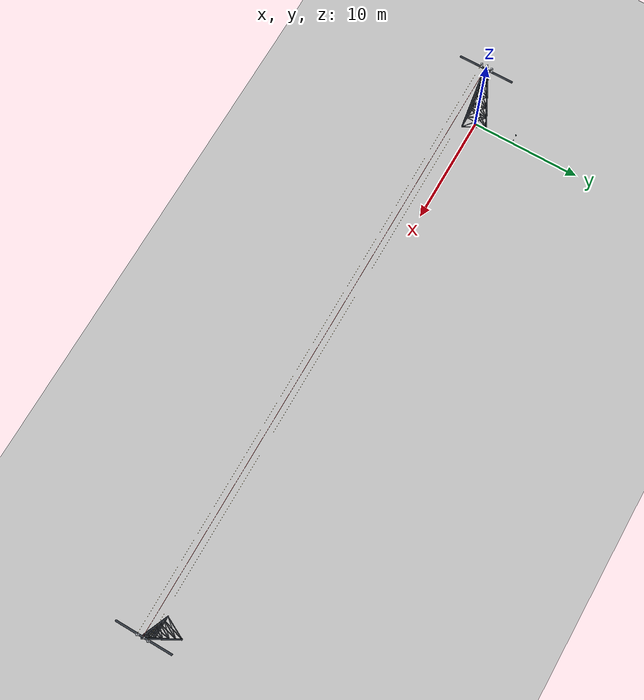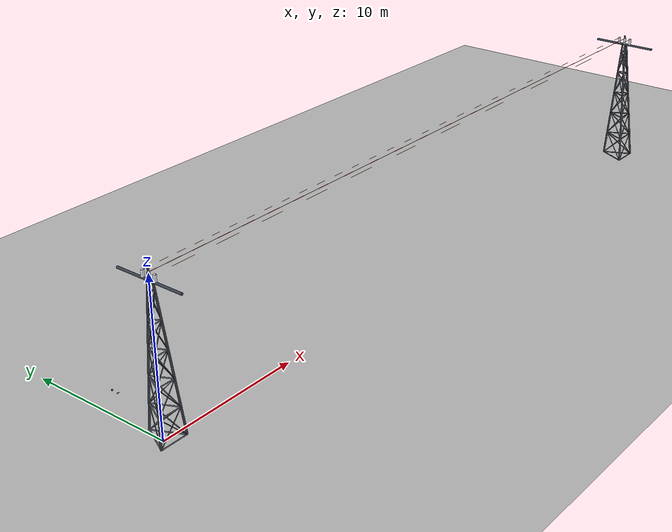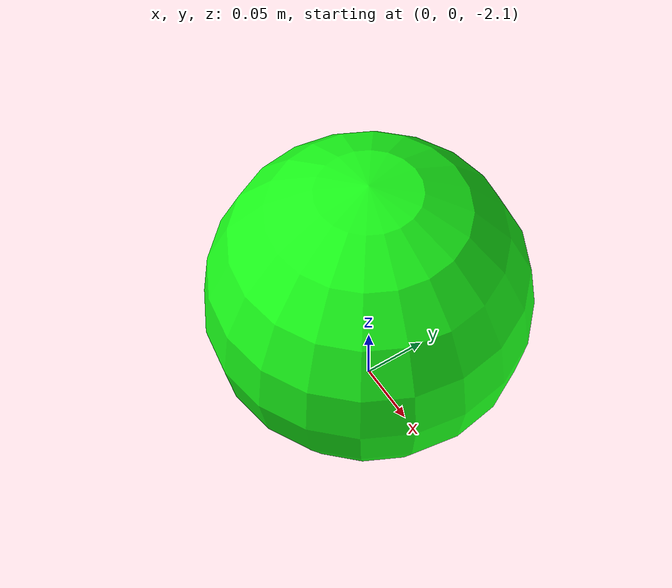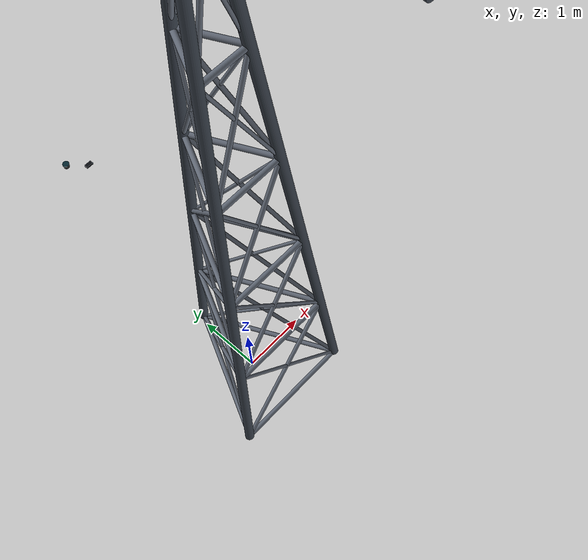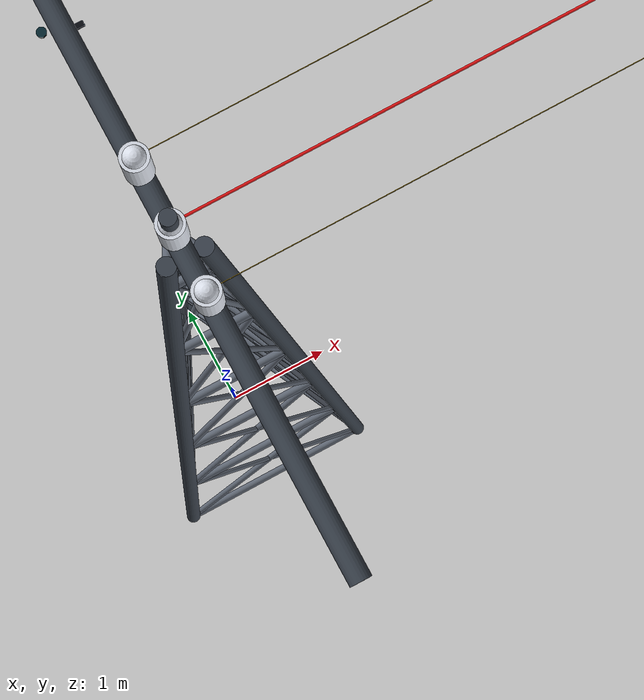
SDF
<sdf version="1.6">
 <world name="inspection_line_world">
  <gravity>0 0 -9.81</gravity>
  <scene>
   <ambient>0.45 0.45 0.45 1</ambient>
   <background>0.72 0.78 0.86 1</background>
   <shadows>true</shadows>
  </scene>
  <physics type="ode">
   <max_step_size>0.001</max_step_size>
   <real_time_update_rate>1000</real_time_update_rate>
  </physics>
  <include><uri>model://sun</uri></include>
  <include><uri>model://ground_plane</uri></include>
  <include>
   <uri>model://inspection_depth_camera</uri>
   <name>inspection_d435i</name>
   <pose>0.35 3.8 1.32 0 0 0</pose>
  </include>
  <include>
   <uri>model://inspection_lidar</uri>
   <name>inspection_mid360</name>
   <pose>0.0 3.8 1.68 0 0 0</pose>
  </include>
  <plugin name="gazebo_ros_state" filename="libgazebo_ros_state.so">
   <ros><namespace>/gazebo</namespace></ros>
   <update_rate>30.0</update_rate>
  </plugin>
  <model name="inspection_scene">
   <static>true</static>
   <link name="scene_link">
    <inertial>
     <mass>1</mass>
     <inertia><ixx>1</ixx><iyy>1</iyy><izz>1</izz><ixy>0</ixy><ixz>0</ixz><iyz>0</iyz></inertia>
    </inertial>
    <visual name="conductor_0">
     <pose>25.000000 -0.450000 10.080000 0.000000 1.570796 0.000000</pose>
     <geometry><cylinder><radius>0.003</radius><length>50.0</length></cylinder></geometry>
     <material>
      <ambient>0.780000 0.640000 0.200000 1.000000</ambient>
      <diffuse>0.780000 0.640000 0.200000 1.000000</diffuse>
      <specular>0.18 0.18 0.18 1</specular>
     </material>
    </visual>
    <visual name="conductor_1">
     <pose>25.000000 0.000000 10.080000 0.000000 1.570796 0.000000</pose>
     <geometry><cylinder><radius>0.003</radius><length>50.0</length></cylinder></geometry>
     <material>
      <ambient>0.780000 0.640000 0.200000 1.000000</ambient>
      <diffuse>0.780000 0.640000 0.200000 1.000000</diffuse>
      <specular>0.18 0.18 0.18 1</specular>
     </material>
    </visual>
    <visual name="conductor_2">
     <pose>25.000000 0.450000 10.080000 0.000000 1.570796 0.000000</pose>
     <geometry><cylinder><radius>0.003</radius><length>50.0</length></cylinder></geometry>
     <material>
      <ambient>0.780000 0.640000 0.200000 1.000000</ambient>
      <diffuse>0.780000 0.640000 0.200000 1.000000</diffuse>
      <specular>0.18 0.18 0.18 1</specular>
     </material>
    </visual>
    <visual name="line_safety_indicator">
     <pose>25.000000 0.000000 10.080000 0.000000 1.570796 0.000000</pose>
     <geometry><cylinder><radius>0.009</radius><length>50.0</length></cylinder></geometry>
     <material>
      <ambient>0.920000 0.080000 0.080000 1.000000</ambient>
      <diffuse>0.920000 0.080000 0.080000 1.000000</diffuse>
      <specular>0.18 0.18 0.18 1</specular>
      <transparency>0.880000</transparency>
     </material>
    </visual>
    <visual name="tower_0_leg_0">
     <pose>-0.527120 -0.497749 4.925000 0.000000 0.117955 0.760403</pose>
     <geometry><cylinder><radius>0.065000</radius><length>9.314725</length></cylinder></geometry>
     <material>
      <ambient>0.220000 0.250000 0.290000 1.000000</ambient>
      <diffuse>0.220000 0.250000 0.290000 1.000000</diffuse>
      <specular>0.18 0.18 0.18 1</specular>
     </material>
    </visual>
    <visual name="tower_0_leg_1">
     <pose>0.527120 -0.497749 4.925000 0.000000 0.117955 2.381189</pose>
     <geometry><cylinder><radius>0.065000</radius><length>9.314725</length></cylinder></geometry>
     <material>
      <ambient>0.220000 0.250000 0.290000 1.000000</ambient>
      <diffuse>0.220000 0.250000 0.290000 1.000000</diffuse>
      <specular>0.18 0.18 0.18 1</specular>
     </material>
    </visual>
    <visual name="tower_0_leg_2">
     <pose>0.000000 0.580707 4.925000 0.000000 0.095001 -1.570796</pose>
     <geometry><cylinder><radius>0.065000</radius><length>9.291899</length></cylinder></geometry>
     <material>
      <ambient>0.220000 0.250000 0.290000 1.000000</ambient>
      <diffuse>0.220000 0.250000 0.290000 1.000000</diffuse>
      <specular>0.18 0.18 0.18 1</specular>
     </material>
    </visual>
    <visual name="tower_0_ring_030_0">
     <pose>0.000000 -0.875497 0.300000 0.000000 1.570796 0.000000</pose>
     <geometry><cylinder><radius>0.035000</radius><length>1.848482</length></cylinder></geometry>
     <material>
      <ambient>0.380000 0.410000 0.460000 1.000000</ambient>
      <diffuse>0.380000 0.410000 0.460000 1.000000</diffuse>
      <specular>0.18 0.18 0.18 1</specular>
     </material>
    </visual>
    <visual name="tower_0_ring_030_1">
     <pose>0.462120 0.072958 0.300000 0.000000 1.570796 2.024180</pose>
     <geometry><cylinder><radius>0.035000</radius><length>2.110093</length></cylinder></geometry>
     <material>
      <ambient>0.380000 0.410000 0.460000 1.000000</ambient>
      <diffuse>0.380000 0.410000 0.460000 1.000000</diffuse>
      <specular>0.18 0.18 0.18 1</specular>
     </material>
    </visual>
    <visual name="tower_0_ring_030_2">
     <pose>-0.462120 0.072958 0.300000 0.000000 1.570796 -2.024180</pose>
     <geometry><cylinder><radius>0.035000</radius><length>2.110093</length></cylinder></geometry>
     <material>
      <ambient>0.380000 0.410000 0.460000 1.000000</ambient>
      <diffuse>0.380000 0.410000 0.460000 1.000000</diffuse>
      <specular>0.18 0.18 0.18 1</specular>
     </material>
    </visual>
    <visual name="tower_0_ring_204_0">
     <pose>0.000000 -0.732565 2.050000 0.000000 1.570796 0.000000</pose>
     <geometry><cylinder><radius>0.035000</radius><length>1.547958</length></cylinder></geometry>
     <material>
      <ambient>0.380000 0.410000 0.460000 1.000000</ambient>
      <diffuse>0.380000 0.410000 0.460000 1.000000</diffuse>
      <specular>0.18 0.18 0.18 1</specular>
     </material>
    </visual>
    <visual name="tower_0_ring_204_1">
     <pose>0.386990 0.061047 2.050000 0.000000 1.570796 2.024499</pose>
     <geometry><cylinder><radius>0.035000</radius><length>1.765879</length></cylinder></geometry>
     <material>
      <ambient>0.380000 0.410000 0.460000 1.000000</ambient>
      <diffuse>0.380000 0.410000 0.460000 1.000000</diffuse>
      <specular>0.18 0.18 0.18 1</specular>
     </material>
    </visual>
    <visual name="tower_0_ring_204_2">
     <pose>-0.386990 0.061047 2.050000 0.000000 1.570796 -2.024499</pose>
     <geometry><cylinder><radius>0.035000</radius><length>1.765879</length></cylinder></geometry>
     <material>
      <ambient>0.380000 0.410000 0.460000 1.000000</ambient>
      <diffuse>0.380000 0.410000 0.460000 1.000000</diffuse>
      <specular>0.18 0.18 0.18 1</specular>
     </material>
    </visual>
    <visual name="tower_0_ring_380_0">
     <pose>0.000000 -0.589634 3.800000 0.000000 1.570796 0.000000</pose>
     <geometry><cylinder><radius>0.035000</radius><length>1.247435</length></cylinder></geometry>
     <material>
      <ambient>0.380000 0.410000 0.460000 1.000000</ambient>
      <diffuse>0.380000 0.410000 0.460000 1.000000</diffuse>
      <specular>0.18 0.18 0.18 1</specular>
     </material>
    </visual>
    <visual name="tower_0_ring_380_1">
     <pose>0.311859 0.049136 3.800000 0.000000 1.570796 2.024974</pose>
     <geometry><cylinder><radius>0.035000</radius><length>1.421664</length></cylinder></geometry>
     <material>
      <ambient>0.380000 0.410000 0.460000 1.000000</ambient>
      <diffuse>0.380000 0.410000 0.460000 1.000000</diffuse>
      <specular>0.18 0.18 0.18 1</specular>
     </material>
    </visual>
    <visual name="tower_0_ring_380_2">
     <pose>-0.311859 0.049136 3.800000 0.000000 1.570796 -2.024974</pose>
     <geometry><cylinder><radius>0.035000</radius><length>1.421664</length></cylinder></geometry>
     <material>
      <ambient>0.380000 0.410000 0.460000 1.000000</ambient>
      <diffuse>0.380000 0.410000 0.460000 1.000000</diffuse>
      <specular>0.18 0.18 0.18 1</specular>
     </material>
    </visual>
    <visual name="tower_0_ring_555_0">
     <pose>0.000000 -0.446702 5.550000 0.000000 1.570796 0.000000</pose>
     <geometry><cylinder><radius>0.035000</radius><length>0.946911</length></cylinder></geometry>
     <material>
      <ambient>0.380000 0.410000 0.460000 1.000000</ambient>
      <diffuse>0.380000 0.410000 0.460000 1.000000</diffuse>
      <specular>0.18 0.18 0.18 1</specular>
     </material>
    </visual>
    <visual name="tower_0_ring_555_1">
     <pose>0.236728 0.037225 5.550000 0.000000 1.570796 2.025751</pose>
     <geometry><cylinder><radius>0.035000</radius><length>1.077451</length></cylinder></geometry>
     <material>
      <ambient>0.380000 0.410000 0.460000 1.000000</ambient>
      <diffuse>0.380000 0.410000 0.460000 1.000000</diffuse>
      <specular>0.18 0.18 0.18 1</specular>
     </material>
    </visual>
    <visual name="tower_0_ring_555_2">
     <pose>-0.236728 0.037225 5.550000 0.000000 1.570796 -2.025751</pose>
     <geometry><cylinder><radius>0.035000</radius><length>1.077451</length></cylinder></geometry>
     <material>
      <ambient>0.380000 0.410000 0.460000 1.000000</ambient>
      <diffuse>0.380000 0.410000 0.460000 1.000000</diffuse>
      <specular>0.18 0.18 0.18 1</specular>
     </material>
    </visual>
    <visual name="tower_0_ring_730_0">
     <pose>0.000000 -0.303770 7.300000 0.000000 1.570796 0.000000</pose>
     <geometry><cylinder><radius>0.035000</radius><length>0.646387</length></cylinder></geometry>
     <material>
      <ambient>0.380000 0.410000 0.460000 1.000000</ambient>
      <diffuse>0.380000 0.410000 0.460000 1.000000</diffuse>
      <specular>0.18 0.18 0.18 1</specular>
     </material>
    </visual>
    <visual name="tower_0_ring_730_1">
     <pose>0.161597 0.025314 7.300000 0.000000 1.570796 2.027259</pose>
     <geometry><cylinder><radius>0.035000</radius><length>0.733238</length></cylinder></geometry>
     <material>
      <ambient>0.380000 0.410000 0.460000 1.000000</ambient>
      <diffuse>0.380000 0.410000 0.460000 1.000000</diffuse>
      <specular>0.18 0.18 0.18 1</specular>
     </material>
    </visual>
    <visual name="tower_0_ring_730_2">
     <pose>-0.161597 0.025314 7.300000 0.000000 1.570796 -2.027259</pose>
     <geometry><cylinder><radius>0.035000</radius><length>0.733238</length></cylinder></geometry>
     <material>
      <ambient>0.380000 0.410000 0.460000 1.000000</ambient>
      <diffuse>0.380000 0.410000 0.460000 1.000000</diffuse>
      <specular>0.18 0.18 0.18 1</specular>
     </material>
    </visual>
    <visual name="tower_0_ring_905_0">
     <pose>0.000000 -0.160838 9.050000 0.000000 1.570796 0.000000</pose>
     <geometry><cylinder><radius>0.035000</radius><length>0.345864</length></cylinder></geometry>
     <material>
      <ambient>0.380000 0.410000 0.460000 1.000000</ambient>
      <diffuse>0.380000 0.410000 0.460000 1.000000</diffuse>
      <specular>0.18 0.18 0.18 1</specular>
     </material>
    </visual>
    <visual name="tower_0_ring_905_1">
     <pose>0.086466 0.013403 9.050000 0.000000 1.570796 2.031435</pose>
     <geometry><cylinder><radius>0.035000</radius><length>0.389031</length></cylinder></geometry>
     <material>
      <ambient>0.380000 0.410000 0.460000 1.000000</ambient>
      <diffuse>0.380000 0.410000 0.460000 1.000000</diffuse>
      <specular>0.18 0.18 0.18 1</specular>
     </material>
    </visual>
    <visual name="tower_0_ring_905_2">
     <pose>-0.086466 0.013403 9.050000 0.000000 1.570796 -2.031435</pose>
     <geometry><cylinder><radius>0.035000</radius><length>0.389031</length></cylinder></geometry>
     <material>
      <ambient>0.380000 0.410000 0.460000 1.000000</ambient>
      <diffuse>0.380000 0.410000 0.460000 1.000000</diffuse>
      <specular>0.18 0.18 0.18 1</specular>
     </material>
    </visual>
    <visual name="tower_0_diag_030_0">
     <pose>-0.075131 -0.804031 1.175000 0.000000 0.772147 0.083968</pose>
     <geometry><cylinder><radius>0.028000</radius><length>2.442720</length></cylinder></geometry>
     <material>
      <ambient>0.380000 0.410000 0.460000 1.000000</ambient>
      <diffuse>0.380000 0.410000 0.460000 1.000000</diffuse>
      <specular>0.18 0.18 0.18 1</specular>
     </material>
    </visual>
    <visual name="tower_0_diag_back_030_0">
     <pose>0.075131 -0.804031 1.175000 0.000000 0.772147 3.057625</pose>
     <geometry><cylinder><radius>0.022000</radius><length>2.442720</length></cylinder></geometry>
     <material>
      <ambient>0.380000 0.410000 0.460000 1.000000</ambient>
      <diffuse>0.380000 0.410000 0.460000 1.000000</diffuse>
      <specular>0.18 0.18 0.18 1</specular>
     </material>
    </visual>
    <visual name="tower_0_diag_030_1">
     <pose>0.462120 -0.010419 1.175000 0.000000 0.842333 2.061424</pose>
     <geometry><cylinder><radius>0.028000</radius><length>2.628719</length></cylinder></geometry>
     <material>
      <ambient>0.380000 0.410000 0.460000 1.000000</ambient>
      <diffuse>0.380000 0.410000 0.460000 1.000000</diffuse>
      <specular>0.18 0.18 0.18 1</specular>
     </material>
    </visual>
    <visual name="tower_0_diag_back_030_1">
     <pose>0.386990 0.144424 1.175000 0.000000 0.830948 -1.155226</pose>
     <geometry><cylinder><radius>0.022000</radius><length>2.595763</length></cylinder></geometry>
     <material>
      <ambient>0.380000 0.410000 0.460000 1.000000</ambient>
      <diffuse>0.380000 0.410000 0.460000 1.000000</diffuse>
      <specular>0.18 0.18 0.18 1</specular>
     </material>
    </visual>
    <visual name="tower_0_diag_030_2">
     <pose>-0.386990 0.144424 1.175000 0.000000 0.830948 -1.986367</pose>
     <geometry><cylinder><radius>0.028000</radius><length>2.595763</length></cylinder></geometry>
     <material>
      <ambient>0.380000 0.410000 0.460000 1.000000</ambient>
      <diffuse>0.380000 0.410000 0.460000 1.000000</diffuse>
      <specular>0.18 0.18 0.18 1</specular>
     </material>
    </visual>
    <visual name="tower_0_diag_back_030_2">
     <pose>-0.462120 -0.010419 1.175000 0.000000 0.842333 1.080169</pose>
     <geometry><cylinder><radius>0.022000</radius><length>2.628719</length></cylinder></geometry>
     <material>
      <ambient>0.380000 0.410000 0.460000 1.000000</ambient>
      <diffuse>0.380000 0.410000 0.460000 1.000000</diffuse>
      <specular>0.18 0.18 0.18 1</specular>
     </material>
    </visual>
    <visual name="tower_0_diag_204_0">
     <pose>-0.075131 -0.661099 2.925000 0.000000 0.676476 0.101908</pose>
     <geometry><cylinder><radius>0.028000</radius><length>2.244211</length></cylinder></geometry>
     <material>
      <ambient>0.380000 0.410000 0.460000 1.000000</ambient>
      <diffuse>0.380000 0.410000 0.460000 1.000000</diffuse>
      <specular>0.18 0.18 0.18 1</specular>
     </material>
    </visual>
    <visual name="tower_0_diag_back_204_0">
     <pose>0.075131 -0.661099 2.925000 0.000000 0.676476 3.039684</pose>
     <geometry><cylinder><radius>0.022000</radius><length>2.244211</length></cylinder></geometry>
     <material>
      <ambient>0.380000 0.410000 0.460000 1.000000</ambient>
      <diffuse>0.380000 0.410000 0.460000 1.000000</diffuse>
      <specular>0.18 0.18 0.18 1</specular>
     </material>
    </visual>
    <visual name="tower_0_diag_204_1">
     <pose>0.386990 -0.022330 2.925000 0.000000 0.746117 2.069696</pose>
     <geometry><cylinder><radius>0.028000</radius><length>2.383124</length></cylinder></geometry>
     <material>
      <ambient>0.380000 0.410000 0.460000 1.000000</ambient>
      <diffuse>0.380000 0.410000 0.460000 1.000000</diffuse>
      <specular>0.18 0.18 0.18 1</specular>
     </material>
    </visual>
    <visual name="tower_0_diag_back_204_1">
     <pose>0.311859 0.132513 2.925000 0.000000 0.732251 -1.163138</pose>
     <geometry><cylinder><radius>0.022000</radius><length>2.353191</length></cylinder></geometry>
     <material>
      <ambient>0.380000 0.410000 0.460000 1.000000</ambient>
      <diffuse>0.380000 0.410000 0.460000 1.000000</diffuse>
      <specular>0.18 0.18 0.18 1</specular>
     </material>
    </visual>
    <visual name="tower_0_diag_204_2">
     <pose>-0.311859 0.132513 2.925000 0.000000 0.732251 -1.978454</pose>
     <geometry><cylinder><radius>0.028000</radius><length>2.353191</length></cylinder></geometry>
     <material>
      <ambient>0.380000 0.410000 0.460000 1.000000</ambient>
      <diffuse>0.380000 0.410000 0.460000 1.000000</diffuse>
      <specular>0.18 0.18 0.18 1</specular>
     </material>
    </visual>
    <visual name="tower_0_diag_back_204_2">
     <pose>-0.386990 -0.022330 2.925000 0.000000 0.746117 1.071896</pose>
     <geometry><cylinder><radius>0.022000</radius><length>2.383124</length></cylinder></geometry>
     <material>
      <ambient>0.380000 0.410000 0.460000 1.000000</ambient>
      <diffuse>0.380000 0.410000 0.460000 1.000000</diffuse>
      <specular>0.18 0.18 0.18 1</specular>
     </material>
    </visual>
    <visual name="tower_0_diag_380_0">
     <pose>-0.075131 -0.518168 4.675000 0.000000 0.563798 0.129543</pose>
     <geometry><cylinder><radius>0.028000</radius><length>2.070439</length></cylinder></geometry>
     <material>
      <ambient>0.380000 0.410000 0.460000 1.000000</ambient>
      <diffuse>0.380000 0.410000 0.460000 1.000000</diffuse>
      <specular>0.18 0.18 0.18 1</specular>
     </material>
    </visual>
    <visual name="tower_0_diag_back_380_0">
     <pose>0.075131 -0.518168 4.675000 0.000000 0.563798 3.012049</pose>
     <geometry><cylinder><radius>0.022000</radius><length>2.070439</length></cylinder></geometry>
     <material>
      <ambient>0.380000 0.410000 0.460000 1.000000</ambient>
      <diffuse>0.380000 0.410000 0.460000 1.000000</diffuse>
      <specular>0.18 0.18 0.18 1</specular>
     </material>
    </visual>
    <visual name="tower_0_diag_380_1">
     <pose>0.311859 -0.034241 4.675000 0.000000 0.629241 2.082434</pose>
     <geometry><cylinder><radius>0.028000</radius><length>2.164571</length></cylinder></geometry>
     <material>
      <ambient>0.380000 0.410000 0.460000 1.000000</ambient>
      <diffuse>0.380000 0.410000 0.460000 1.000000</diffuse>
      <specular>0.18 0.18 0.18 1</specular>
     </material>
    </visual>
    <visual name="tower_0_diag_back_380_1">
     <pose>0.236728 0.120602 4.675000 0.000000 0.612422 -1.175478</pose>
     <geometry><cylinder><radius>0.022000</radius><length>2.138690</length></cylinder></geometry>
     <material>
      <ambient>0.380000 0.410000 0.460000 1.000000</ambient>
      <diffuse>0.380000 0.410000 0.460000 1.000000</diffuse>
      <specular>0.18 0.18 0.18 1</specular>
     </material>
    </visual>
    <visual name="tower_0_diag_380_2">
     <pose>-0.236728 0.120602 4.675000 0.000000 0.612422 -1.966115</pose>
     <geometry><cylinder><radius>0.028000</radius><length>2.138690</length></cylinder></geometry>
     <material>
      <ambient>0.380000 0.410000 0.460000 1.000000</ambient>
      <diffuse>0.380000 0.410000 0.460000 1.000000</diffuse>
      <specular>0.18 0.18 0.18 1</specular>
     </material>
    </visual>
    <visual name="tower_0_diag_back_380_2">
     <pose>-0.311859 -0.034241 4.675000 0.000000 0.629241 1.059159</pose>
     <geometry><cylinder><radius>0.022000</radius><length>2.164571</length></cylinder></geometry>
     <material>
      <ambient>0.380000 0.410000 0.460000 1.000000</ambient>
      <diffuse>0.380000 0.410000 0.460000 1.000000</diffuse>
      <specular>0.18 0.18 0.18 1</specular>
     </material>
    </visual>
    <visual name="tower_0_diag_555_0">
     <pose>-0.075131 -0.375236 6.425000 0.000000 0.433198 0.177528</pose>
     <geometry><cylinder><radius>0.028000</radius><length>1.928103</length></cylinder></geometry>
     <material>
      <ambient>0.380000 0.410000 0.460000 1.000000</ambient>
      <diffuse>0.380000 0.410000 0.460000 1.000000</diffuse>
      <specular>0.18 0.18 0.18 1</specular>
     </material>
    </visual>
    <visual name="tower_0_diag_back_555_0">
     <pose>0.075131 -0.375236 6.425000 0.000000 0.433198 2.964065</pose>
     <geometry><cylinder><radius>0.022000</radius><length>1.928103</length></cylinder></geometry>
     <material>
      <ambient>0.380000 0.410000 0.460000 1.000000</ambient>
      <diffuse>0.380000 0.410000 0.460000 1.000000</diffuse>
      <specular>0.18 0.18 0.18 1</specular>
     </material>
    </visual>
    <visual name="tower_0_diag_555_1">
     <pose>0.236728 -0.046152 6.425000 0.000000 0.488718 2.104577</pose>
     <geometry><cylinder><radius>0.028000</radius><length>1.982024</length></cylinder></geometry>
     <material>
      <ambient>0.380000 0.410000 0.460000 1.000000</ambient>
      <diffuse>0.380000 0.410000 0.460000 1.000000</diffuse>
      <specular>0.18 0.18 0.18 1</specular>
     </material>
    </visual>
    <visual name="tower_0_diag_back_555_1">
     <pose>0.161597 0.108691 6.425000 0.000000 0.468652 -1.197390</pose>
     <geometry><cylinder><radius>0.022000</radius><length>1.961492</length></cylinder></geometry>
     <material>
      <ambient>0.380000 0.410000 0.460000 1.000000</ambient>
      <diffuse>0.380000 0.410000 0.460000 1.000000</diffuse>
      <specular>0.18 0.18 0.18 1</specular>
     </material>
    </visual>
    <visual name="tower_0_diag_555_2">
     <pose>-0.161597 0.108691 6.425000 0.000000 0.468652 -1.944203</pose>
     <geometry><cylinder><radius>0.028000</radius><length>1.961492</length></cylinder></geometry>
     <material>
      <ambient>0.380000 0.410000 0.460000 1.000000</ambient>
      <diffuse>0.380000 0.410000 0.460000 1.000000</diffuse>
      <specular>0.18 0.18 0.18 1</specular>
     </material>
    </visual>
    <visual name="tower_0_diag_back_555_2">
     <pose>-0.236728 -0.046152 6.425000 0.000000 0.488718 1.037015</pose>
     <geometry><cylinder><radius>0.022000</radius><length>1.982024</length></cylinder></geometry>
     <material>
      <ambient>0.380000 0.410000 0.460000 1.000000</ambient>
      <diffuse>0.380000 0.410000 0.460000 1.000000</diffuse>
      <specular>0.18 0.18 0.18 1</specular>
     </material>
    </visual>
    <visual name="tower_0_diag_730_0">
     <pose>-0.075131 -0.232304 8.175000 0.000000 0.286892 0.280500</pose>
     <geometry><cylinder><radius>0.028000</radius><length>1.824574</length></cylinder></geometry>
     <material>
      <ambient>0.380000 0.410000 0.460000 1.000000</ambient>
      <diffuse>0.380000 0.410000 0.460000 1.000000</diffuse>
      <specular>0.18 0.18 0.18 1</specular>
     </material>
    </visual>
    <visual name="tower_0_diag_back_730_0">
     <pose>0.075131 -0.232304 8.175000 0.000000 0.286892 2.861092</pose>
     <geometry><cylinder><radius>0.022000</radius><length>1.824574</length></cylinder></geometry>
     <material>
      <ambient>0.380000 0.410000 0.460000 1.000000</ambient>
      <diffuse>0.380000 0.410000 0.460000 1.000000</diffuse>
      <specular>0.18 0.18 0.18 1</specular>
     </material>
    </visual>
    <visual name="tower_0_diag_730_1">
     <pose>0.161597 -0.058063 8.175000 0.000000 0.324235 2.152553</pose>
     <geometry><cylinder><radius>0.028000</radius><length>1.846197</length></cylinder></geometry>
     <material>
      <ambient>0.380000 0.410000 0.460000 1.000000</ambient>
      <diffuse>0.380000 0.410000 0.460000 1.000000</diffuse>
      <specular>0.18 0.18 0.18 1</specular>
     </material>
    </visual>
    <visual name="tower_0_diag_back_730_1">
     <pose>0.086466 0.096780 8.175000 0.000000 0.301118 -1.246974</pose>
     <geometry><cylinder><radius>0.022000</radius><length>1.832450</length></cylinder></geometry>
     <material>
      <ambient>0.380000 0.410000 0.460000 1.000000</ambient>
      <diffuse>0.380000 0.410000 0.460000 1.000000</diffuse>
      <specular>0.18 0.18 0.18 1</specular>
     </material>
    </visual>
    <visual name="tower_0_diag_730_2">
     <pose>-0.086466 0.096780 8.175000 0.000000 0.301118 -1.894618</pose>
     <geometry><cylinder><radius>0.028000</radius><length>1.832450</length></cylinder></geometry>
     <material>
      <ambient>0.380000 0.410000 0.460000 1.000000</ambient>
      <diffuse>0.380000 0.410000 0.460000 1.000000</diffuse>
      <specular>0.18 0.18 0.18 1</specular>
     </material>
    </visual>
    <visual name="tower_0_diag_back_730_2">
     <pose>-0.161597 -0.058063 8.175000 0.000000 0.324235 0.989040</pose>
     <geometry><cylinder><radius>0.022000</radius><length>1.846197</length></cylinder></geometry>
     <material>
      <ambient>0.380000 0.410000 0.460000 1.000000</ambient>
      <diffuse>0.380000 0.410000 0.460000 1.000000</diffuse>
      <specular>0.18 0.18 0.18 1</specular>
     </material>
    </visual>
    <visual name="tower_0_crossarm">
     <pose>0.000000 0.000000 9.620000 0.000000 1.570796 1.570796</pose>
     <geometry><cylinder><radius>0.075000</radius><length>4.700000</length></cylinder></geometry>
     <material>
      <ambient>0.220000 0.250000 0.290000 1.000000</ambient>
      <diffuse>0.220000 0.250000 0.290000 1.000000</diffuse>
      <specular>0.18 0.18 0.18 1</specular>
     </material>
    </visual>
    <visual name="tower_0_top_mast">
     <pose>0.000000 0.000000 9.950000 0.000000 0.000000 0.000000</pose>
     <geometry><cylinder><radius>0.055000</radius><length>0.700000</length></cylinder></geometry>
     <material>
      <ambient>0.220000 0.250000 0.290000 1.000000</ambient>
      <diffuse>0.220000 0.250000 0.290000 1.000000</diffuse>
      <specular>0.18 0.18 0.18 1</specular>
     </material>
    </visual>
    <visual name="tower_0_insulator_0">
     <pose>0.000000 -0.450000 9.880000 0.000000 0.000000 0.000000</pose>
     <geometry><cylinder><radius>0.095000</radius><length>0.420000</length></cylinder></geometry>
     <material>
      <ambient>0.860000 0.880000 0.920000 1.000000</ambient>
      <diffuse>0.860000 0.880000 0.920000 1.000000</diffuse>
      <specular>0.18 0.18 0.18 1</specular>
     </material>
    </visual>
    <visual name="tower_0_cap_0">
     <pose>0.000000 -0.450000 10.080000 0.000000 0.000000 0.000000</pose>
     <geometry><sphere><radius>0.075000</radius></sphere></geometry>
     <material>
      <ambient>0.860000 0.880000 0.920000 1.000000</ambient>
      <diffuse>0.860000 0.880000 0.920000 1.000000</diffuse>
      <specular>0.18 0.18 0.18 1</specular>
     </material>
    </visual>
    <visual name="tower_0_insulator_1">
     <pose>0.000000 0.000000 9.880000 0.000000 0.000000 0.000000</pose>
     <geometry><cylinder><radius>0.095000</radius><length>0.420000</length></cylinder></geometry>
     <material>
      <ambient>0.860000 0.880000 0.920000 1.000000</ambient>
      <diffuse>0.860000 0.880000 0.920000 1.000000</diffuse>
      <specular>0.18 0.18 0.18 1</specular>
     </material>
    </visual>
    <visual name="tower_0_cap_1">
     <pose>0.000000 0.000000 10.080000 0.000000 0.000000 0.000000</pose>
     <geometry><sphere><radius>0.075000</radius></sphere></geometry>
     <material>
      <ambient>0.860000 0.880000 0.920000 1.000000</ambient>
      <diffuse>0.860000 0.880000 0.920000 1.000000</diffuse>
      <specular>0.18 0.18 0.18 1</specular>
     </material>
    </visual>
    <visual name="tower_0_insulator_2">
     <pose>0.000000 0.450000 9.880000 0.000000 0.000000 0.000000</pose>
     <geometry><cylinder><radius>0.095000</radius><length>0.420000</length></cylinder></geometry>
     <material>
      <ambient>0.860000 0.880000 0.920000 1.000000</ambient>
      <diffuse>0.860000 0.880000 0.920000 1.000000</diffuse>
      <specular>0.18 0.18 0.18 1</specular>
     </material>
    </visual>
    <visual name="tower_0_cap_2">
     <pose>0.000000 0.450000 10.080000 0.000000 0.000000 0.000000</pose>
     <geometry><sphere><radius>0.075000</radius></sphere></geometry>
     <material>
      <ambient>0.860000 0.880000 0.920000 1.000000</ambient>
      <diffuse>0.860000 0.880000 0.920000 1.000000</diffuse>
      <specular>0.18 0.18 0.18 1</specular>
     </material>
    </visual>
    <visual name="tower_50_leg_0">
     <pose>49.472880 -0.497749 4.925000 0.000000 0.117955 0.760403</pose>
     <geometry><cylinder><radius>0.065000</radius><length>9.314725</length></cylinder></geometry>
     <material>
      <ambient>0.220000 0.250000 0.290000 1.000000</ambient>
      <diffuse>0.220000 0.250000 0.290000 1.000000</diffuse>
      <specular>0.18 0.18 0.18 1</specular>
     </material>
    </visual>
    <visual name="tower_50_leg_1">
     <pose>50.527120 -0.497749 4.925000 0.000000 0.117955 2.381189</pose>
     <geometry><cylinder><radius>0.065000</radius><length>9.314725</length></cylinder></geometry>
     <material>
      <ambient>0.220000 0.250000 0.290000 1.000000</ambient>
      <diffuse>0.220000 0.250000 0.290000 1.000000</diffuse>
      <specular>0.18 0.18 0.18 1</specular>
     </material>
    </visual>
    <visual name="tower_50_leg_2">
     <pose>50.000000 0.580707 4.925000 0.000000 0.095001 -1.570796</pose>
     <geometry><cylinder><radius>0.065000</radius><length>9.291899</length></cylinder></geometry>
     <material>
      <ambient>0.220000 0.250000 0.290000 1.000000</ambient>
      <diffuse>0.220000 0.250000 0.290000 1.000000</diffuse>
      <specular>0.18 0.18 0.18 1</specular>
     </material>
    </visual>
    <visual name="tower_50_ring_030_0">
     <pose>50.000000 -0.875497 0.300000 0.000000 1.570796 0.000000</pose>
     <geometry><cylinder><radius>0.035000</radius><length>1.848482</length></cylinder></geometry>
     <material>
      <ambient>0.380000 0.410000 0.460000 1.000000</ambient>
      <diffuse>0.380000 0.410000 0.460000 1.000000</diffuse>
      <specular>0.18 0.18 0.18 1</specular>
     </material>
    </visual>
    <visual name="tower_50_ring_030_1">
     <pose>50.462120 0.072958 0.300000 0.000000 1.570796 2.024180</pose>
     <geometry><cylinder><radius>0.035000</radius><length>2.110093</length></cylinder></geometry>
     <material>
      <ambient>0.380000 0.410000 0.460000 1.000000</ambient>
      <diffuse>0.380000 0.410000 0.460000 1.000000</diffuse>
      <specular>0.18 0.18 0.18 1</specular>
     </material>
    </visual>
    <visual name="tower_50_ring_030_2">
     <pose>49.537880 0.072958 0.300000 0.000000 1.570796 -2.024180</pose>
     <geometry><cylinder><radius>0.035000</radius><length>2.110093</length></cylinder></geometry>
     <material>
      <ambient>0.380000 0.410000 0.460000 1.000000</ambient>
      <diffuse>0.380000 0.410000 0.460000 1.000000</diffuse>
      <specular>0.18 0.18 0.18 1</specular>
     </material>
    </visual>
    <visual name="tower_50_ring_204_0">
     <pose>50.000000 -0.732565 2.050000 0.000000 1.570796 0.000000</pose>
     <geometry><cylinder><radius>0.035000</radius><length>1.547958</length></cylinder></geometry>
     <material>
      <ambient>0.380000 0.410000 0.460000 1.000000</ambient>
      <diffuse>0.380000 0.410000 0.460000 1.000000</diffuse>
      <specular>0.18 0.18 0.18 1</specular>
     </material>
    </visual>
    <visual name="tower_50_ring_204_1">
     <pose>50.386990 0.061047 2.050000 0.000000 1.570796 2.024499</pose>
     <geometry><cylinder><radius>0.035000</radius><length>1.765879</length></cylinder></geometry>
     <material>
      <ambient>0.380000 0.410000 0.460000 1.000000</ambient>
      <diffuse>0.380000 0.410000 0.460000 1.000000</diffuse>
      <specular>0.18 0.18 0.18 1</specular>
     </material>
    </visual>
    <visual name="tower_50_ring_204_2">
     <pose>49.613010 0.061047 2.050000 0.000000 1.570796 -2.024499</pose>
     <geometry><cylinder><radius>0.035000</radius><length>1.765879</length></cylinder></geometry>
     <material>
      <ambient>0.380000 0.410000 0.460000 1.000000</ambient>
      <diffuse>0.380000 0.410000 0.460000 1.000000</diffuse>
      <specular>0.18 0.18 0.18 1</specular>
     </material>
    </visual>
    <visual name="tower_50_ring_380_0">
     <pose>50.000000 -0.589634 3.800000 0.000000 1.570796 0.000000</pose>
     <geometry><cylinder><radius>0.035000</radius><length>1.247435</length></cylinder></geometry>
     <material>
      <ambient>0.380000 0.410000 0.460000 1.000000</ambient>
      <diffuse>0.380000 0.410000 0.460000 1.000000</diffuse>
      <specular>0.18 0.18 0.18 1</specular>
     </material>
    </visual>
    <visual name="tower_50_ring_380_1">
     <pose>50.311859 0.049136 3.800000 0.000000 1.570796 2.024974</pose>
     <geometry><cylinder><radius>0.035000</radius><length>1.421664</length></cylinder></geometry>
     <material>
      <ambient>0.380000 0.410000 0.460000 1.000000</ambient>
      <diffuse>0.380000 0.410000 0.460000 1.000000</diffuse>
      <specular>0.18 0.18 0.18 1</specular>
     </material>
    </visual>
    <visual name="tower_50_ring_380_2">
     <pose>49.688141 0.049136 3.800000 0.000000 1.570796 -2.024974</pose>
     <geometry><cylinder><radius>0.035000</radius><length>1.421664</length></cylinder></geometry>
     <material>
      <ambient>0.380000 0.410000 0.460000 1.000000</ambient>
      <diffuse>0.380000 0.410000 0.460000 1.000000</diffuse>
      <specular>0.18 0.18 0.18 1</specular>
     </material>
    </visual>
    <visual name="tower_50_ring_555_0">
     <pose>50.000000 -0.446702 5.550000 0.000000 1.570796 0.000000</pose>
     <geometry><cylinder><radius>0.035000</radius><length>0.946911</length></cylinder></geometry>
     <material>
      <ambient>0.380000 0.410000 0.460000 1.000000</ambient>
      <diffuse>0.380000 0.410000 0.460000 1.000000</diffuse>
      <specular>0.18 0.18 0.18 1</specular>
     </material>
    </visual>
    <visual name="tower_50_ring_555_1">
     <pose>50.236728 0.037225 5.550000 0.000000 1.570796 2.025751</pose>
     <geometry><cylinder><radius>0.035000</radius><length>1.077451</length></cylinder></geometry>
     <material>
      <ambient>0.380000 0.410000 0.460000 1.000000</ambient>
      <diffuse>0.380000 0.410000 0.460000 1.000000</diffuse>
      <specular>0.18 0.18 0.18 1</specular>
     </material>
    </visual>
    <visual name="tower_50_ring_555_2">
     <pose>49.763272 0.037225 5.550000 0.000000 1.570796 -2.025751</pose>
     <geometry><cylinder><radius>0.035000</radius><length>1.077451</length></cylinder></geometry>
     <material>
      <ambient>0.380000 0.410000 0.460000 1.000000</ambient>
      <diffuse>0.380000 0.410000 0.460000 1.000000</diffuse>
      <specular>0.18 0.18 0.18 1</specular>
     </material>
    </visual>
    <visual name="tower_50_ring_730_0">
     <pose>50.000000 -0.303770 7.300000 0.000000 1.570796 0.000000</pose>
     <geometry><cylinder><radius>0.035000</radius><length>0.646387</length></cylinder></geometry>
     <material>
      <ambient>0.380000 0.410000 0.460000 1.000000</ambient>
      <diffuse>0.380000 0.410000 0.460000 1.000000</diffuse>
      <specular>0.18 0.18 0.18 1</specular>
     </material>
    </visual>
    <visual name="tower_50_ring_730_1">
     <pose>50.161597 0.025314 7.300000 0.000000 1.570796 2.027259</pose>
     <geometry><cylinder><radius>0.035000</radius><length>0.733238</length></cylinder></geometry>
     <material>
      <ambient>0.380000 0.410000 0.460000 1.000000</ambient>
      <diffuse>0.380000 0.410000 0.460000 1.000000</diffuse>
      <specular>0.18 0.18 0.18 1</specular>
     </material>
    </visual>
    <visual name="tower_50_ring_730_2">
     <pose>49.838403 0.025314 7.300000 0.000000 1.570796 -2.027259</pose>
     <geometry><cylinder><radius>0.035000</radius><length>0.733238</length></cylinder></geometry>
     <material>
      <ambient>0.380000 0.410000 0.460000 1.000000</ambient>
      <diffuse>0.380000 0.410000 0.460000 1.000000</diffuse>
      <specular>0.18 0.18 0.18 1</specular>
     </material>
    </visual>
    <visual name="tower_50_ring_905_0">
     <pose>50.000000 -0.160838 9.050000 0.000000 1.570796 0.000000</pose>
     <geometry><cylinder><radius>0.035000</radius><length>0.345864</length></cylinder></geometry>
     <material>
      <ambient>0.380000 0.410000 0.460000 1.000000</ambient>
      <diffuse>0.380000 0.410000 0.460000 1.000000</diffuse>
      <specular>0.18 0.18 0.18 1</specular>
     </material>
    </visual>
    <visual name="tower_50_ring_905_1">
     <pose>50.086466 0.013403 9.050000 0.000000 1.570796 2.031435</pose>
     <geometry><cylinder><radius>0.035000</radius><length>0.389031</length></cylinder></geometry>
     <material>
      <ambient>0.380000 0.410000 0.460000 1.000000</ambient>
      <diffuse>0.380000 0.410000 0.460000 1.000000</diffuse>
      <specular>0.18 0.18 0.18 1</specular>
     </material>
    </visual>
    <visual name="tower_50_ring_905_2">
     <pose>49.913534 0.013403 9.050000 0.000000 1.570796 -2.031435</pose>
     <geometry><cylinder><radius>0.035000</radius><length>0.389031</length></cylinder></geometry>
     <material>
      <ambient>0.380000 0.410000 0.460000 1.000000</ambient>
      <diffuse>0.380000 0.410000 0.460000 1.000000</diffuse>
      <specular>0.18 0.18 0.18 1</specular>
     </material>
    </visual>
    <visual name="tower_50_diag_030_0">
     <pose>49.924869 -0.804031 1.175000 0.000000 0.772147 0.083968</pose>
     <geometry><cylinder><radius>0.028000</radius><length>2.442720</length></cylinder></geometry>
     <material>
      <ambient>0.380000 0.410000 0.460000 1.000000</ambient>
      <diffuse>0.380000 0.410000 0.460000 1.000000</diffuse>
      <specular>0.18 0.18 0.18 1</specular>
     </material>
    </visual>
    <visual name="tower_50_diag_back_030_0">
     <pose>50.075131 -0.804031 1.175000 0.000000 0.772147 3.057625</pose>
     <geometry><cylinder><radius>0.022000</radius><length>2.442720</length></cylinder></geometry>
     <material>
      <ambient>0.380000 0.410000 0.460000 1.000000</ambient>
      <diffuse>0.380000 0.410000 0.460000 1.000000</diffuse>
      <specular>0.18 0.18 0.18 1</specular>
     </material>
    </visual>
    <visual name="tower_50_diag_030_1">
     <pose>50.462120 -0.010419 1.175000 0.000000 0.842333 2.061424</pose>
     <geometry><cylinder><radius>0.028000</radius><length>2.628719</length></cylinder></geometry>
     <material>
      <ambient>0.380000 0.410000 0.460000 1.000000</ambient>
      <diffuse>0.380000 0.410000 0.460000 1.000000</diffuse>
      <specular>0.18 0.18 0.18 1</specular>
     </material>
    </visual>
    <visual name="tower_50_diag_back_030_1">
     <pose>50.386990 0.144424 1.175000 0.000000 0.830948 -1.155226</pose>
     <geometry><cylinder><radius>0.022000</radius><length>2.595763</length></cylinder></geometry>
     <material>
      <ambient>0.380000 0.410000 0.460000 1.000000</ambient>
      <diffuse>0.380000 0.410000 0.460000 1.000000</diffuse>
      <specular>0.18 0.18 0.18 1</specular>
     </material>
    </visual>
    <visual name="tower_50_diag_030_2">
     <pose>49.613010 0.144424 1.175000 0.000000 0.830948 -1.986367</pose>
     <geometry><cylinder><radius>0.028000</radius><length>2.595763</length></cylinder></geometry>
     <material>
      <ambient>0.380000 0.410000 0.460000 1.000000</ambient>
      <diffuse>0.380000 0.410000 0.460000 1.000000</diffuse>
      <specular>0.18 0.18 0.18 1</specular>
     </material>
    </visual>
    <visual name="tower_50_diag_back_030_2">
     <pose>49.537880 -0.010419 1.175000 0.000000 0.842333 1.080169</pose>
     <geometry><cylinder><radius>0.022000</radius><length>2.628719</length></cylinder></geometry>
     <material>
      <ambient>0.380000 0.410000 0.460000 1.000000</ambient>
      <diffuse>0.380000 0.410000 0.460000 1.000000</diffuse>
      <specular>0.18 0.18 0.18 1</specular>
     </material>
    </visual>
    <visual name="tower_50_diag_204_0">
     <pose>49.924869 -0.661099 2.925000 0.000000 0.676476 0.101908</pose>
     <geometry><cylinder><radius>0.028000</radius><length>2.244211</length></cylinder></geometry>
     <material>
      <ambient>0.380000 0.410000 0.460000 1.000000</ambient>
      <diffuse>0.380000 0.410000 0.460000 1.000000</diffuse>
      <specular>0.18 0.18 0.18 1</specular>
     </material>
    </visual>
    <visual name="tower_50_diag_back_204_0">
     <pose>50.075131 -0.661099 2.925000 0.000000 0.676476 3.039684</pose>
     <geometry><cylinder><radius>0.022000</radius><length>2.244211</length></cylinder></geometry>
     <material>
      <ambient>0.380000 0.410000 0.460000 1.000000</ambient>
      <diffuse>0.380000 0.410000 0.460000 1.000000</diffuse>
      <specular>0.18 0.18 0.18 1</specular>
     </material>
    </visual>
    <visual name="tower_50_diag_204_1">
     <pose>50.386990 -0.022330 2.925000 0.000000 0.746117 2.069696</pose>
     <geometry><cylinder><radius>0.028000</radius><length>2.383124</length></cylinder></geometry>
     <material>
      <ambient>0.380000 0.410000 0.460000 1.000000</ambient>
      <diffuse>0.380000 0.410000 0.460000 1.000000</diffuse>
      <specular>0.18 0.18 0.18 1</specular>
     </material>
    </visual>
    <visual name="tower_50_diag_back_204_1">
     <pose>50.311859 0.132513 2.925000 0.000000 0.732251 -1.163138</pose>
     <geometry><cylinder><radius>0.022000</radius><length>2.353191</length></cylinder></geometry>
     <material>
      <ambient>0.380000 0.410000 0.460000 1.000000</ambient>
      <diffuse>0.380000 0.410000 0.460000 1.000000</diffuse>
      <specular>0.18 0.18 0.18 1</specular>
     </material>
    </visual>
    <visual name="tower_50_diag_204_2">
     <pose>49.688141 0.132513 2.925000 0.000000 0.732251 -1.978454</pose>
     <geometry><cylinder><radius>0.028000</radius><length>2.353191</length></cylinder></geometry>
     <material>
      <ambient>0.380000 0.410000 0.460000 1.000000</ambient>
      <diffuse>0.380000 0.410000 0.460000 1.000000</diffuse>
      <specular>0.18 0.18 0.18 1</specular>
     </material>
    </visual>
    <visual name="tower_50_diag_back_204_2">
     <pose>49.613010 -0.022330 2.925000 0.000000 0.746117 1.071896</pose>
     <geometry><cylinder><radius>0.022000</radius><length>2.383124</length></cylinder></geometry>
     <material>
      <ambient>0.380000 0.410000 0.460000 1.000000</ambient>
      <diffuse>0.380000 0.410000 0.460000 1.000000</diffuse>
      <specular>0.18 0.18 0.18 1</specular>
     </material>
    </visual>
    <visual name="tower_50_diag_380_0">
     <pose>49.924869 -0.518168 4.675000 0.000000 0.563798 0.129543</pose>
     <geometry><cylinder><radius>0.028000</radius><length>2.070439</length></cylinder></geometry>
     <material>
      <ambient>0.380000 0.410000 0.460000 1.000000</ambient>
      <diffuse>0.380000 0.410000 0.460000 1.000000</diffuse>
      <specular>0.18 0.18 0.18 1</specular>
     </material>
    </visual>
    <visual name="tower_50_diag_back_380_0">
     <pose>50.075131 -0.518168 4.675000 0.000000 0.563798 3.012049</pose>
     <geometry><cylinder><radius>0.022000</radius><length>2.070439</length></cylinder></geometry>
     <material>
      <ambient>0.380000 0.410000 0.460000 1.000000</ambient>
      <diffuse>0.380000 0.410000 0.460000 1.000000</diffuse>
      <specular>0.18 0.18 0.18 1</specular>
     </material>
    </visual>
    <visual name="tower_50_diag_380_1">
     <pose>50.311859 -0.034241 4.675000 0.000000 0.629241 2.082434</pose>
     <geometry><cylinder><radius>0.028000</radius><length>2.164571</length></cylinder></geometry>
     <material>
      <ambient>0.380000 0.410000 0.460000 1.000000</ambient>
      <diffuse>0.380000 0.410000 0.460000 1.000000</diffuse>
      <specular>0.18 0.18 0.18 1</specular>
     </material>
    </visual>
    <visual name="tower_50_diag_back_380_1">
     <pose>50.236728 0.120602 4.675000 0.000000 0.612422 -1.175478</pose>
     <geometry><cylinder><radius>0.022000</radius><length>2.138690</length></cylinder></geometry>
     <material>
      <ambient>0.380000 0.410000 0.460000 1.000000</ambient>
      <diffuse>0.380000 0.410000 0.460000 1.000000</diffuse>
      <specular>0.18 0.18 0.18 1</specular>
     </material>
    </visual>
    <visual name="tower_50_diag_380_2">
     <pose>49.763272 0.120602 4.675000 0.000000 0.612422 -1.966115</pose>
     <geometry><cylinder><radius>0.028000</radius><length>2.138690</length></cylinder></geometry>
     <material>
      <ambient>0.380000 0.410000 0.460000 1.000000</ambient>
      <diffuse>0.380000 0.410000 0.460000 1.000000</diffuse>
      <specular>0.18 0.18 0.18 1</specular>
     </material>
    </visual>
    <visual name="tower_50_diag_back_380_2">
     <pose>49.688141 -0.034241 4.675000 0.000000 0.629241 1.059159</pose>
     <geometry><cylinder><radius>0.022000</radius><length>2.164571</length></cylinder></geometry>
     <material>
      <ambient>0.380000 0.410000 0.460000 1.000000</ambient>
      <diffuse>0.380000 0.410000 0.460000 1.000000</diffuse>
      <specular>0.18 0.18 0.18 1</specular>
     </material>
    </visual>
    <visual name="tower_50_diag_555_0">
     <pose>49.924869 -0.375236 6.425000 0.000000 0.433198 0.177528</pose>
     <geometry><cylinder><radius>0.028000</radius><length>1.928103</length></cylinder></geometry>
     <material>
      <ambient>0.380000 0.410000 0.460000 1.000000</ambient>
      <diffuse>0.380000 0.410000 0.460000 1.000000</diffuse>
      <specular>0.18 0.18 0.18 1</specular>
     </material>
    </visual>
    <visual name="tower_50_diag_back_555_0">
     <pose>50.075131 -0.375236 6.425000 0.000000 0.433198 2.964065</pose>
     <geometry><cylinder><radius>0.022000</radius><length>1.928103</length></cylinder></geometry>
     <material>
      <ambient>0.380000 0.410000 0.460000 1.000000</ambient>
      <diffuse>0.380000 0.410000 0.460000 1.000000</diffuse>
      <specular>0.18 0.18 0.18 1</specular>
     </material>
    </visual>
    <visual name="tower_50_diag_555_1">
     <pose>50.236728 -0.046152 6.425000 0.000000 0.488718 2.104577</pose>
     <geometry><cylinder><radius>0.028000</radius><length>1.982024</length></cylinder></geometry>
     <material>
      <ambient>0.380000 0.410000 0.460000 1.000000</ambient>
      <diffuse>0.380000 0.410000 0.460000 1.000000</diffuse>
      <specular>0.18 0.18 0.18 1</specular>
     </material>
    </visual>
    <visual name="tower_50_diag_back_555_1">
     <pose>50.161597 0.108691 6.425000 0.000000 0.468652 -1.197390</pose>
     <geometry><cylinder><radius>0.022000</radius><length>1.961492</length></cylinder></geometry>
     <material>
      <ambient>0.380000 0.410000 0.460000 1.000000</ambient>
      <diffuse>0.380000 0.410000 0.460000 1.000000</diffuse>
      <specular>0.18 0.18 0.18 1</specular>
     </material>
    </visual>
    <visual name="tower_50_diag_555_2">
     <pose>49.838403 0.108691 6.425000 0.000000 0.468652 -1.944203</pose>
     <geometry><cylinder><radius>0.028000</radius><length>1.961492</length></cylinder></geometry>
     <material>
      <ambient>0.380000 0.410000 0.460000 1.000000</ambient>
      <diffuse>0.380000 0.410000 0.460000 1.000000</diffuse>
      <specular>0.18 0.18 0.18 1</specular>
     </material>
    </visual>
    <visual name="tower_50_diag_back_555_2">
     <pose>49.763272 -0.046152 6.425000 0.000000 0.488718 1.037015</pose>
     <geometry><cylinder><radius>0.022000</radius><length>1.982024</length></cylinder></geometry>
     <material>
      <ambient>0.380000 0.410000 0.460000 1.000000</ambient>
      <diffuse>0.380000 0.410000 0.460000 1.000000</diffuse>
      <specular>0.18 0.18 0.18 1</specular>
     </material>
    </visual>
    <visual name="tower_50_diag_730_0">
     <pose>49.924869 -0.232304 8.175000 0.000000 0.286892 0.280500</pose>
     <geometry><cylinder><radius>0.028000</radius><length>1.824574</length></cylinder></geometry>
     <material>
      <ambient>0.380000 0.410000 0.460000 1.000000</ambient>
      <diffuse>0.380000 0.410000 0.460000 1.000000</diffuse>
      <specular>0.18 0.18 0.18 1</specular>
     </material>
    </visual>
    <visual name="tower_50_diag_back_730_0">
     <pose>50.075131 -0.232304 8.175000 0.000000 0.286892 2.861092</pose>
     <geometry><cylinder><radius>0.022000</radius><length>1.824574</length></cylinder></geometry>
     <material>
      <ambient>0.380000 0.410000 0.460000 1.000000</ambient>
      <diffuse>0.380000 0.410000 0.460000 1.000000</diffuse>
      <specular>0.18 0.18 0.18 1</specular>
     </material>
    </visual>
    <visual name="tower_50_diag_730_1">
     <pose>50.161597 -0.058063 8.175000 0.000000 0.324235 2.152553</pose>
     <geometry><cylinder><radius>0.028000</radius><length>1.846197</length></cylinder></geometry>
     <material>
      <ambient>0.380000 0.410000 0.460000 1.000000</ambient>
      <diffuse>0.380000 0.410000 0.460000 1.000000</diffuse>
      <specular>0.18 0.18 0.18 1</specular>
     </material>
    </visual>
    <visual name="tower_50_diag_back_730_1">
     <pose>50.086466 0.096780 8.175000 0.000000 0.301118 -1.246974</pose>
     <geometry><cylinder><radius>0.022000</radius><length>1.832450</length></cylinder></geometry>
     <material>
      <ambient>0.380000 0.410000 0.460000 1.000000</ambient>
      <diffuse>0.380000 0.410000 0.460000 1.000000</diffuse>
      <specular>0.18 0.18 0.18 1</specular>
     </material>
    </visual>
    <visual name="tower_50_diag_730_2">
     <pose>49.913534 0.096780 8.175000 0.000000 0.301118 -1.894618</pose>
     <geometry><cylinder><radius>0.028000</radius><length>1.832450</length></cylinder></geometry>
     <material>
      <ambient>0.380000 0.410000 0.460000 1.000000</ambient>
      <diffuse>0.380000 0.410000 0.460000 1.000000</diffuse>
      <specular>0.18 0.18 0.18 1</specular>
     </material>
    </visual>
    <visual name="tower_50_diag_back_730_2">
     <pose>49.838403 -0.058063 8.175000 0.000000 0.324235 0.989040</pose>
     <geometry><cylinder><radius>0.022000</radius><length>1.846197</length></cylinder></geometry>
     <material>
      <ambient>0.380000 0.410000 0.460000 1.000000</ambient>
      <diffuse>0.380000 0.410000 0.460000 1.000000</diffuse>
      <specular>0.18 0.18 0.18 1</specular>
     </material>
    </visual>
    <visual name="tower_50_crossarm">
     <pose>50.000000 0.000000 9.620000 0.000000 1.570796 1.570796</pose>
     <geometry><cylinder><radius>0.075000</radius><length>4.700000</length></cylinder></geometry>
     <material>
      <ambient>0.220000 0.250000 0.290000 1.000000</ambient>
      <diffuse>0.220000 0.250000 0.290000 1.000000</diffuse>
      <specular>0.18 0.18 0.18 1</specular>
     </material>
    </visual>
    <visual name="tower_50_top_mast">
     <pose>50.000000 0.000000 9.950000 0.000000 0.000000 0.000000</pose>
     <geometry><cylinder><radius>0.055000</radius><length>0.700000</length></cylinder></geometry>
     <material>
      <ambient>0.220000 0.250000 0.290000 1.000000</ambient>
      <diffuse>0.220000 0.250000 0.290000 1.000000</diffuse>
      <specular>0.18 0.18 0.18 1</specular>
     </material>
    </visual>
    <visual name="tower_50_insulator_0">
     <pose>50.000000 -0.450000 9.880000 0.000000 0.000000 0.000000</pose>
     <geometry><cylinder><radius>0.095000</radius><length>0.420000</length></cylinder></geometry>
     <material>
      <ambient>0.860000 0.880000 0.920000 1.000000</ambient>
      <diffuse>0.860000 0.880000 0.920000 1.000000</diffuse>
      <specular>0.18 0.18 0.18 1</specular>
     </material>
    </visual>
    <visual name="tower_50_cap_0">
     <pose>50.000000 -0.450000 10.080000 0.000000 0.000000 0.000000</pose>
     <geometry><sphere><radius>0.075000</radius></sphere></geometry>
     <material>
      <ambient>0.860000 0.880000 0.920000 1.000000</ambient>
      <diffuse>0.860000 0.880000 0.920000 1.000000</diffuse>
      <specular>0.18 0.18 0.18 1</specular>
     </material>
    </visual>
    <visual name="tower_50_insulator_1">
     <pose>50.000000 0.000000 9.880000 0.000000 0.000000 0.000000</pose>
     <geometry><cylinder><radius>0.095000</radius><length>0.420000</length></cylinder></geometry>
     <material>
      <ambient>0.860000 0.880000 0.920000 1.000000</ambient>
      <diffuse>0.860000 0.880000 0.920000 1.000000</diffuse>
      <specular>0.18 0.18 0.18 1</specular>
     </material>
    </visual>
    <visual name="tower_50_cap_1">
     <pose>50.000000 0.000000 10.080000 0.000000 0.000000 0.000000</pose>
     <geometry><sphere><radius>0.075000</radius></sphere></geometry>
     <material>
      <ambient>0.860000 0.880000 0.920000 1.000000</ambient>
      <diffuse>0.860000 0.880000 0.920000 1.000000</diffuse>
      <specular>0.18 0.18 0.18 1</specular>
     </material>
    </visual>
    <visual name="tower_50_insulator_2">
     <pose>50.000000 0.450000 9.880000 0.000000 0.000000 0.000000</pose>
     <geometry><cylinder><radius>0.095000</radius><length>0.420000</length></cylinder></geometry>
     <material>
      <ambient>0.860000 0.880000 0.920000 1.000000</ambient>
      <diffuse>0.860000 0.880000 0.920000 1.000000</diffuse>
      <specular>0.18 0.18 0.18 1</specular>
     </material>
    </visual>
    <visual name="tower_50_cap_2">
     <pose>50.000000 0.450000 10.080000 0.000000 0.000000 0.000000</pose>
     <geometry><sphere><radius>0.075000</radius></sphere></geometry>
     <material>
      <ambient>0.860000 0.880000 0.920000 1.000000</ambient>
      <diffuse>0.860000 0.880000 0.920000 1.000000</diffuse>
      <specular>0.18 0.18 0.18 1</specular>
     </material>
    </visual>
   </link>
  </model>
  <model name="coverage_00">
   <pose>0 0 -2 0 0 0</pose>
   <static>false</static>
   <link name="marker">
    <gravity>false</gravity>
    <kinematic>true</kinematic>
    <inertial>
     <mass>0.01</mass>
     <inertia><ixx>0.001</ixx><iyy>0.001</iyy><izz>0.001</izz><ixy>0</ixy><ixz>0</ixz><iyz>0</iyz></inertia>
    </inertial>
    <visual name="covered_cell">
     <geometry><sphere><radius>0.120000</radius></sphere></geometry>
     <material>
      <ambient>0.100000 1.000000 0.100000 1.000000</ambient>
      <diffuse>0.100000 1.000000 0.100000 1.000000</diffuse>
      <specular>0.18 0.18 0.18 1</specular>
     </material>
    </visual>
   </link>
  </model>
  <model name="coverage_01">
   <pose>0 0 -2 0 0 0</pose>
   <static>false</static>
   <link name="marker">
    <gravity>false</gravity>
    <kinematic>true</kinematic>
    <inertial>
     <mass>0.01</mass>
     <inertia><ixx>0.001</ixx><iyy>0.001</iyy><izz>0.001</izz><ixy>0</ixy><ixz>0</ixz><iyz>0</iyz></inertia>
    </inertial>
    <visual name="covered_cell">
     <geometry><sphere><radius>0.120000</radius></sphere></geometry>
     <material>
      <ambient>0.100000 1.000000 0.100000 1.000000</ambient>
      <diffuse>0.100000 1.000000 0.100000 1.000000</diffuse>
      <specular>0.18 0.18 0.18 1</specular>
     </material>
    </visual>
   </link>
  </model>
  <model name="coverage_02">
   <pose>0 0 -2 0 0 0</pose>
   <static>false</static>
   <link name="marker">
    <gravity>false</gravity>
    <kinematic>true</kinematic>
    <inertial>
     <mass>0.01</mass>
     <inertia><ixx>0.001</ixx><iyy>0.001</iyy><izz>0.001</izz><ixy>0</ixy><ixz>0</ixz><iyz>0</iyz></inertia>
    </inertial>
    <visual name="covered_cell">
     <geometry><sphere><radius>0.120000</radius></sphere></geometry>
     <material>
      <ambient>0.100000 1.000000 0.100000 1.000000</ambient>
      <diffuse>0.100000 1.000000 0.100000 1.000000</diffuse>
      <specular>0.18 0.18 0.18 1</specular>
     </material>
    </visual>
   </link>
  </model>
  <model name="coverage_03">
   <pose>0 0 -2 0 0 0</pose>
   <static>false</static>
   <link name="marker">
    <gravity>false</gravity>
    <kinematic>true</kinematic>
    <inertial>
     <mass>0.01</mass>
     <inertia><ixx>0.001</ixx><iyy>0.001</iyy><izz>0.001</izz><ixy>0</ixy><ixz>0</ixz><iyz>0</iyz></inertia>
    </inertial>
    <visual name="covered_cell">
     <geometry><sphere><radius>0.120000</radius></sphere></geometry>
     <material>
      <ambient>0.100000 1.000000 0.100000 1.000000</ambient>
      <diffuse>0.100000 1.000000 0.100000 1.000000</diffuse>
      <specular>0.18 0.18 0.18 1</specular>
     </material>
    </visual>
   </link>
  </model>
  <model name="coverage_04">
   <pose>0 0 -2 0 0 0</pose>
   <static>false</static>
   <link name="marker">
    <gravity>false</gravity>
    <kinematic>true</kinematic>
    <inertial>
     <mass>0.01</mass>
     <inertia><ixx>0.001</ixx><iyy>0.001</iyy><izz>0.001</izz><ixy>0</ixy><ixz>0</ixz><iyz>0</iyz></inertia>
    </inertial>
    <visual name="covered_cell">
     <geometry><sphere><radius>0.120000</radius></sphere></geometry>
     <material>
      <ambient>0.100000 1.000000 0.100000 1.000000</ambient>
      <diffuse>0.100000 1.000000 0.100000 1.000000</diffuse>
      <specular>0.18 0.18 0.18 1</specular>
     </material>
    </visual>
   </link>
  </model>
  <model name="coverage_05">
   <pose>0 0 -2 0 0 0</pose>
   <static>false</static>
   <link name="marker">
    <gravity>false</gravity>
    <kinematic>true</kinematic>
    <inertial>
     <mass>0.01</mass>
     <inertia><ixx>0.001</ixx><iyy>0.001</iyy><izz>0.001</izz><ixy>0</ixy><ixz>0</ixz><iyz>0</iyz></inertia>
    </inertial>
    <visual name="covered_cell">
     <geometry><sphere><radius>0.120000</radius></sphere></geometry>
     <material>
      <ambient>0.100000 1.000000 0.100000 1.000000</ambient>
      <diffuse>0.100000 1.000000 0.100000 1.000000</diffuse>
      <specular>0.18 0.18 0.18 1</specular>
     </material>
    </visual>
   </link>
  </model>
  <model name="coverage_06">
   <pose>0 0 -2 0 0 0</pose>
   <static>false</static>
   <link name="marker">
    <gravity>false</gravity>
    <kinematic>true</kinematic>
    <inertial>
     <mass>0.01</mass>
     <inertia><ixx>0.001</ixx><iyy>0.001</iyy><izz>0.001</izz><ixy>0</ixy><ixz>0</ixz><iyz>0</iyz></inertia>
    </inertial>
    <visual name="covered_cell">
     <geometry><sphere><radius>0.120000</radius></sphere></geometry>
     <material>
      <ambient>0.100000 1.000000 0.100000 1.000000</ambient>
      <diffuse>0.100000 1.000000 0.100000 1.000000</diffuse>
      <specular>0.18 0.18 0.18 1</specular>
     </material>
    </visual>
   </link>
  </model>
  <model name="coverage_07">
   <pose>0 0 -2 0 0 0</pose>
   <static>false</static>
   <link name="marker">
    <gravity>false</gravity>
    <kinematic>true</kinematic>
    <inertial>
     <mass>0.01</mass>
     <inertia><ixx>0.001</ixx><iyy>0.001</iyy><izz>0.001</izz><ixy>0</ixy><ixz>0</ixz><iyz>0</iyz></inertia>
    </inertial>
    <visual name="covered_cell">
     <geometry><sphere><radius>0.120000</radius></sphere></geometry>
     <material>
      <ambient>0.100000 1.000000 0.100000 1.000000</ambient>
      <diffuse>0.100000 1.000000 0.100000 1.000000</diffuse>
      <specular>0.18 0.18 0.18 1</specular>
     </material>
    </visual>
   </link>
  </model>
  <model name="coverage_08">
   <pose>0 0 -2 0 0 0</pose>
   <static>false</static>
   <link name="marker">
    <gravity>false</gravity>
    <kinematic>true</kinematic>
    <inertial>
     <mass>0.01</mass>
     <inertia><ixx>0.001</ixx><iyy>0.001</iyy><izz>0.001</izz><ixy>0</ixy><ixz>0</ixz><iyz>0</iyz></inertia>
    </inertial>
    <visual name="covered_cell">
     <geometry><sphere><radius>0.120000</radius></sphere></geometry>
     <material>
      <ambient>0.100000 1.000000 0.100000 1.000000</ambient>
      <diffuse>0.100000 1.000000 0.100000 1.000000</diffuse>
      <specular>0.18 0.18 0.18 1</specular>
     </material>
    </visual>
   </link>
  </model>
  <model name="coverage_09">
   <pose>0 0 -2 0 0 0</pose>
   <static>false</static>
   <link name="marker">
    <gravity>false</gravity>
    <kinematic>true</kinematic>
    <inertial>
     <mass>0.01</mass>
     <inertia><ixx>0.001</ixx><iyy>0.001</iyy><izz>0.001</izz><ixy>0</ixy><ixz>0</ixz><iyz>0</iyz></inertia>
    </inertial>
    <visual name="covered_cell">
     <geometry><sphere><radius>0.120000</radius></sphere></geometry>
     <material>
      <ambient>0.100000 1.000000 0.100000 1.000000</ambient>
      <diffuse>0.100000 1.000000 0.100000 1.000000</diffuse>
      <specular>0.18 0.18 0.18 1</specular>
     </material>
    </visual>
   </link>
  </model>
  <model name="coverage_10">
   <pose>0 0 -2 0 0 0</pose>
   <static>false</static>
   <link name="marker">
    <gravity>false</gravity>
    <kinematic>true</kinematic>
    <inertial>
     <mass>0.01</mass>
     <inertia><ixx>0.001</ixx><iyy>0.001</iyy><izz>0.001</izz><ixy>0</ixy><ixz>0</ixz><iyz>0</iyz></inertia>
    </inertial>
    <visual name="covered_cell">
     <geometry><sphere><radius>0.120000</radius></sphere></geometry>
     <material>
      <ambient>0.100000 1.000000 0.100000 1.000000</ambient>
      <diffuse>0.100000 1.000000 0.100000 1.000000</diffuse>
      <specular>0.18 0.18 0.18 1</specular>
     </material>
    </visual>
   </link>
  </model>
  <model name="coverage_11">
   <pose>0 0 -2 0 0 0</pose>
   <static>false</static>
   <link name="marker">
    <gravity>false</gravity>
    <kinematic>true</kinematic>
    <inertial>
     <mass>0.01</mass>
     <inertia><ixx>0.001</ixx><iyy>0.001</iyy><izz>0.001</izz><ixy>0</ixy><ixz>0</ixz><iyz>0</iyz></inertia>
    </inertial>
    <visual name="covered_cell">
     <geometry><sphere><radius>0.120000</radius></sphere></geometry>
     <material>
      <ambient>0.100000 1.000000 0.100000 1.000000</ambient>
      <diffuse>0.100000 1.000000 0.100000 1.000000</diffuse>
      <specular>0.18 0.18 0.18 1</specular>
     </material>
    </visual>
   </link>
  </model>
  <model name="coverage_12">
   <pose>0 0 -2 0 0 0</pose>
   <static>false</static>
   <link name="marker">
    <gravity>false</gravity>
    <kinematic>true</kinematic>
    <inertial>
     <mass>0.01</mass>
     <inertia><ixx>0.001</ixx><iyy>0.001</iyy><izz>0.001</izz><ixy>0</ixy><ixz>0</ixz><iyz>0</iyz></inertia>
    </inertial>
    <visual name="covered_cell">
     <geometry><sphere><radius>0.120000</radius></sphere></geometry>
     <material>
      <ambient>0.100000 1.000000 0.100000 1.000000</ambient>
      <diffuse>0.100000 1.000000 0.100000 1.000000</diffuse>
      <specular>0.18 0.18 0.18 1</specular>
     </material>
    </visual>
   </link>
  </model>
  <model name="coverage_13">
   <pose>0 0 -2 0 0 0</pose>
   <static>false</static>
   <link name="marker">
    <gravity>false</gravity>
    <kinematic>true</kinematic>
    <inertial>
     <mass>0.01</mass>
     <inertia><ixx>0.001</ixx><iyy>0.001</iyy><izz>0.001</izz><ixy>0</ixy><ixz>0</ixz><iyz>0</iyz></inertia>
    </inertial>
    <visual name="covered_cell">
     <geometry><sphere><radius>0.120000</radius></sphere></geometry>
     <material>
      <ambient>0.100000 1.000000 0.100000 1.000000</ambient>
      <diffuse>0.100000 1.000000 0.100000 1.000000</diffuse>
      <specular>0.18 0.18 0.18 1</specular>
     </material>
    </visual>
   </link>
  </model>
  <model name="coverage_14">
   <pose>0 0 -2 0 0 0</pose>
   <static>false</static>
   <link name="marker">
    <gravity>false</gravity>
    <kinematic>true</kinematic>
    <inertial>
     <mass>0.01</mass>
     <inertia><ixx>0.001</ixx><iyy>0.001</iyy><izz>0.001</izz><ixy>0</ixy><ixz>0</ixz><iyz>0</iyz></inertia>
    </inertial>
    <visual name="covered_cell">
     <geometry><sphere><radius>0.120000</radius></sphere></geometry>
     <material>
      <ambient>0.100000 1.000000 0.100000 1.000000</ambient>
      <diffuse>0.100000 1.000000 0.100000 1.000000</diffuse>
      <specular>0.18 0.18 0.18 1</specular>
     </material>
    </visual>
   </link>
  </model>
  <model name="coverage_15">
   <pose>0 0 -2 0 0 0</pose>
   <static>false</static>
   <link name="marker">
    <gravity>false</gravity>
    <kinematic>true</kinematic>
    <inertial>
     <mass>0.01</mass>
     <inertia><ixx>0.001</ixx><iyy>0.001</iyy><izz>0.001</izz><ixy>0</ixy><ixz>0</ixz><iyz>0</iyz></inertia>
    </inertial>
    <visual name="covered_cell">
     <geometry><sphere><radius>0.120000</radius></sphere></geometry>
     <material>
      <ambient>0.100000 1.000000 0.100000 1.000000</ambient>
      <diffuse>0.100000 1.000000 0.100000 1.000000</diffuse>
      <specular>0.18 0.18 0.18 1</specular>
     </material>
    </visual>
   </link>
  </model>
  <model name="coverage_16">
   <pose>0 0 -2 0 0 0</pose>
   <static>false</static>
   <link name="marker">
    <gravity>false</gravity>
    <kinematic>true</kinematic>
    <inertial>
     <mass>0.01</mass>
     <inertia><ixx>0.001</ixx><iyy>0.001</iyy><izz>0.001</izz><ixy>0</ixy><ixz>0</ixz><iyz>0</iyz></inertia>
    </inertial>
    <visual name="covered_cell">
     <geometry><sphere><radius>0.120000</radius></sphere></geometry>
     <material>
      <ambient>0.100000 1.000000 0.100000 1.000000</ambient>
      <diffuse>0.100000 1.000000 0.100000 1.000000</diffuse>
      <specular>0.18 0.18 0.18 1</specular>
     </material>
    </visual>
   </link>
  </model>
  <model name="coverage_17">
   <pose>0 0 -2 0 0 0</pose>
   <static>false</static>
   <link name="marker">
    <gravity>false</gravity>
    <kinematic>true</kinematic>
    <inertial>
     <mass>0.01</mass>
     <inertia><ixx>0.001</ixx><iyy>0.001</iyy><izz>0.001</izz><ixy>0</ixy><ixz>0</ixz><iyz>0</iyz></inertia>
    </inertial>
    <visual name="covered_cell">
     <geometry><sphere><radius>0.120000</radius></sphere></geometry>
     <material>
      <ambient>0.100000 1.000000 0.100000 1.000000</ambient>
      <diffuse>0.100000 1.000000 0.100000 1.000000</diffuse>
      <specular>0.18 0.18 0.18 1</specular>
     </material>
    </visual>
   </link>
  </model>
  <model name="coverage_18">
   <pose>0 0 -2 0 0 0</pose>
   <static>false</static>
   <link name="marker">
    <gravity>false</gravity>
    <kinematic>true</kinematic>
    <inertial>
     <mass>0.01</mass>
     <inertia><ixx>0.001</ixx><iyy>0.001</iyy><izz>0.001</izz><ixy>0</ixy><ixz>0</ixz><iyz>0</iyz></inertia>
    </inertial>
    <visual name="covered_cell">
     <geometry><sphere><radius>0.120000</radius></sphere></geometry>
     <material>
      <ambient>0.100000 1.000000 0.100000 1.000000</ambient>
      <diffuse>0.100000 1.000000 0.100000 1.000000</diffuse>
      <specular>0.18 0.18 0.18 1</specular>
     </material>
    </visual>
   </link>
  </model>
  <model name="coverage_19">
   <pose>0 0 -2 0 0 0</pose>
   <static>false</static>
   <link name="marker">
    <gravity>false</gravity>
    <kinematic>true</kinematic>
    <inertial>
     <mass>0.01</mass>
     <inertia><ixx>0.001</ixx><iyy>0.001</iyy><izz>0.001</izz><ixy>0</ixy><ixz>0</ixz><iyz>0</iyz></inertia>
    </inertial>
    <visual name="covered_cell">
     <geometry><sphere><radius>0.120000</radius></sphere></geometry>
     <material>
      <ambient>0.100000 1.000000 0.100000 1.000000</ambient>
      <diffuse>0.100000 1.000000 0.100000 1.000000</diffuse>
      <specular>0.18 0.18 0.18 1</specular>
     </material>
    </visual>
   </link>
  </model>
  <model name="coverage_20">
   <pose>0 0 -2 0 0 0</pose>
   <static>false</static>
   <link name="marker">
    <gravity>false</gravity>
    <kinematic>true</kinematic>
    <inertial>
     <mass>0.01</mass>
     <inertia><ixx>0.001</ixx><iyy>0.001</iyy><izz>0.001</izz><ixy>0</ixy><ixz>0</ixz><iyz>0</iyz></inertia>
    </inertial>
    <visual name="covered_cell">
     <geometry><sphere><radius>0.120000</radius></sphere></geometry>
     <material>
      <ambient>0.100000 1.000000 0.100000 1.000000</ambient>
      <diffuse>0.100000 1.000000 0.100000 1.000000</diffuse>
      <specular>0.18 0.18 0.18 1</specular>
     </material>
    </visual>
   </link>
  </model>
  <model name="coverage_21">
   <pose>0 0 -2 0 0 0</pose>
   <static>false</static>
   <link name="marker">
    <gravity>false</gravity>
    <kinematic>true</kinematic>
    <inertial>
     <mass>0.01</mass>
     <inertia><ixx>0.001</ixx><iyy>0.001</iyy><izz>0.001</izz><ixy>0</ixy><ixz>0</ixz><iyz>0</iyz></inertia>
    </inertial>
    <visual name="covered_cell">
     <geometry><sphere><radius>0.120000</radius></sphere></geometry>
     <material>
      <ambient>0.100000 1.000000 0.100000 1.000000</ambient>
      <diffuse>0.100000 1.000000 0.100000 1.000000</diffuse>
      <specular>0.18 0.18 0.18 1</specular>
     </material>
    </visual>
   </link>
  </model>
  <model name="coverage_22">
   <pose>0 0 -2 0 0 0</pose>
   <static>false</static>
   <link name="marker">
    <gravity>false</gravity>
    <kinematic>true</kinematic>
    <inertial>
     <mass>0.01</mass>
     <inertia><ixx>0.001</ixx><iyy>0.001</iyy><izz>0.001</izz><ixy>0</ixy><ixz>0</ixz><iyz>0</iyz></inertia>
    </inertial>
    <visual name="covered_cell">
     <geometry><sphere><radius>0.120000</radius></sphere></geometry>
     <material>
      <ambient>0.100000 1.000000 0.100000 1.000000</ambient>
      <diffuse>0.100000 1.000000 0.100000 1.000000</diffuse>
      <specular>0.18 0.18 0.18 1</specular>
     </material>
    </visual>
   </link>
  </model>
  <model name="coverage_23">
   <pose>0 0 -2 0 0 0</pose>
   <static>false</static>
   <link name="marker">
    <gravity>false</gravity>
    <kinematic>true</kinematic>
    <inertial>
     <mass>0.01</mass>
     <inertia><ixx>0.001</ixx><iyy>0.001</iyy><izz>0.001</izz><ixy>0</ixy><ixz>0</ixz><iyz>0</iyz></inertia>
    </inertial>
    <visual name="covered_cell">
     <geometry><sphere><radius>0.120000</radius></sphere></geometry>
     <material>
      <ambient>0.100000 1.000000 0.100000 1.000000</ambient>
      <diffuse>0.100000 1.000000 0.100000 1.000000</diffuse>
      <specular>0.18 0.18 0.18 1</specular>
     </material>
    </visual>
   </link>
  </model>
  <model name="coverage_24">
   <pose>0 0 -2 0 0 0</pose>
   <static>false</static>
   <link name="marker">
    <gravity>false</gravity>
    <kinematic>true</kinematic>
    <inertial>
     <mass>0.01</mass>
     <inertia><ixx>0.001</ixx><iyy>0.001</iyy><izz>0.001</izz><ixy>0</ixy><ixz>0</ixz><iyz>0</iyz></inertia>
    </inertial>
    <visual name="covered_cell">
     <geometry><sphere><radius>0.120000</radius></sphere></geometry>
     <material>
      <ambient>0.100000 1.000000 0.100000 1.000000</ambient>
      <diffuse>0.100000 1.000000 0.100000 1.000000</diffuse>
      <specular>0.18 0.18 0.18 1</specular>
     </material>
    </visual>
   </link>
  </model>
 </world>
</sdf>

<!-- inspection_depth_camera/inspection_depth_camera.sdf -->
<sdf version="1.5">
  <model name="inspection_depth_camera">
    <pose>0 0 0.035 0 0 0</pose>
    <link name="link">
      <gravity>false</gravity>
      <kinematic>true</kinematic>
      <inertial>
        <pose>0.01 0.025 0.025 0 0 0</pose>
        <mass>0.01</mass>
        <inertia>
          <ixx>4.15e-6</ixx>
          <ixy>0</ixy>
          <ixz>0</ixz>
          <iyy>2.407e-6</iyy>
          <iyz>0</iyz>
          <izz>2.407e-6</izz>
        </inertia>
      </inertial>
      <visual name="visual">
        <!-- Primitive housing keeps this ROS demo independent of PX4's
             optional realsense_camera mesh path. -->
        <geometry><box><size>0.12 0.06 0.04</size></box></geometry>
        <material><ambient>0.04 0.05 0.07 1</ambient><diffuse>0.04 0.05 0.07 1</diffuse><specular>0.35 0.35 0.40 1</specular></material>
      </visual>
      <visual name="left_lens">
        <pose>0.062 -0.018 0 0 1.570796 0</pose>
        <geometry><cylinder><radius>0.010</radius><length>0.004</length></cylinder></geometry>
        <material><ambient>0.02 0.18 0.28 1</ambient><diffuse>0.02 0.18 0.28 1</diffuse><specular>0.7 0.8 0.9 1</specular></material>
      </visual>
      <visual name="right_lens">
        <pose>0.062 0.018 0 0 1.570796 0</pose>
        <geometry><cylinder><radius>0.010</radius><length>0.004</length></cylinder></geometry>
        <material><ambient>0.02 0.18 0.28 1</ambient><diffuse>0.02 0.18 0.28 1</diffuse><specular>0.7 0.8 0.9 1</specular></material>
      </visual>
      <sensor name="d435i_depth" type="depth">
        <always_on>true</always_on>
        <update_rate>15</update_rate>
        <visualize>false</visualize>
        <camera name="d435i_camera">
          <horizontal_fov>1.518436</horizontal_fov>
          <image>
            <format>B8G8R8</format>
            <width>848</width>
            <height>480</height>
          </image>
          <clip>
            <near>0.105</near>
            <far>20.0</far>
          </clip>
          <depth_camera></depth_camera>
          <distortion>
            <k1>0.0</k1>
            <k2>0.0</k2>
            <k3>0.0</k3>
            <p1>0.0</p1>
            <p2>0.0</p2>
            <center>0.5 0.5</center>
          </distortion>
        </camera>
        <plugin name="d435i_ros" filename="libgazebo_ros_camera.so">
          <ros>
            <namespace>/inspection_d435i</namespace>
          </ros>
          <camera_name>d435i</camera_name>
          <frame_name>inspection_d435i_link</frame_name>
          <hack_baseline>0.07</hack_baseline>
          <min_depth>0.105</min_depth>
          <max_depth>20.0</max_depth>
        </plugin>
      </sensor>
    </link>
  </model>
</sdf>

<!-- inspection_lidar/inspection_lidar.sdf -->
<sdf version="1.5">
  <model name="inspection_lidar">
    <link name="link">
      <gravity>false</gravity>
      <kinematic>true</kinematic>
      <inertial>
        <mass>0.25</mass>
        <inertia>
          <ixx>2.2e-5</ixx>
          <ixy>0</ixy>
          <ixz>0</ixz>
          <iyy>2.2e-5</iyy>
          <iyz>0</iyz>
          <izz>2.2e-5</izz>
        </inertia>
      </inertial>
      <visual name="visual">
        <geometry>
          <cylinder>
            <radius>0.045</radius>
            <length>0.060</length>
          </cylinder>
        </geometry>
        <material>
          <ambient>0.08 0.08 0.08 1</ambient>
          <diffuse>0.12 0.12 0.12 1</diffuse>
        </material>
      </visual>
      <visual name="scan_ring">
        <pose>0 0 0.034 0 0 0</pose>
        <geometry><cylinder><radius>0.052</radius><length>0.012</length></cylinder></geometry>
        <material><ambient>0.03 0.16 0.20 1</ambient><diffuse>0.03 0.16 0.20 1</diffuse><specular>0.5 0.65 0.7 1</specular></material>
      </visual>
      <sensor name="mid360" type="ray">
        <always_on>true</always_on>
        <update_rate>10</update_rate>
        <visualize>false</visualize>
        <ray>
          <scan>
            <horizontal>
              <samples>360</samples>
              <resolution>1</resolution>
              <min_angle>-3.14159265359</min_angle>
              <max_angle>3.14159265359</max_angle>
            </horizontal>
            <vertical>
              <samples>16</samples>
              <resolution>1</resolution>
              <min_angle>-0.2617993878</min_angle>
              <max_angle>0.2617993878</max_angle>
            </vertical>
          </scan>
          <range>
            <min>0.10</min>
            <max>70.0</max>
            <resolution>0.01</resolution>
          </range>
          <noise>
            <type>gaussian</type>
            <mean>0.0</mean>
            <stddev>0.01</stddev>
          </noise>
        </ray>
        <!-- This plugin is provided by ros-humble-gazebo-plugins.  The
             PointCloud2 topic is shaped like a MID-360 data stream; it is
             still synthetic Gazebo data, not a hardware driver. -->
        <plugin name="mid360_ros" filename="libgazebo_ros_ray_sensor.so">
          <ros>
            <namespace>/inspection/mid360</namespace>
            <remapping>~/out:=points</remapping>
          </ros>
          <output_type>sensor_msgs/PointCloud2</output_type>
          <frame_name>inspection_mid360_link</frame_name>
        </plugin>
      </sensor>
    </link>
  </model>
</sdf>
